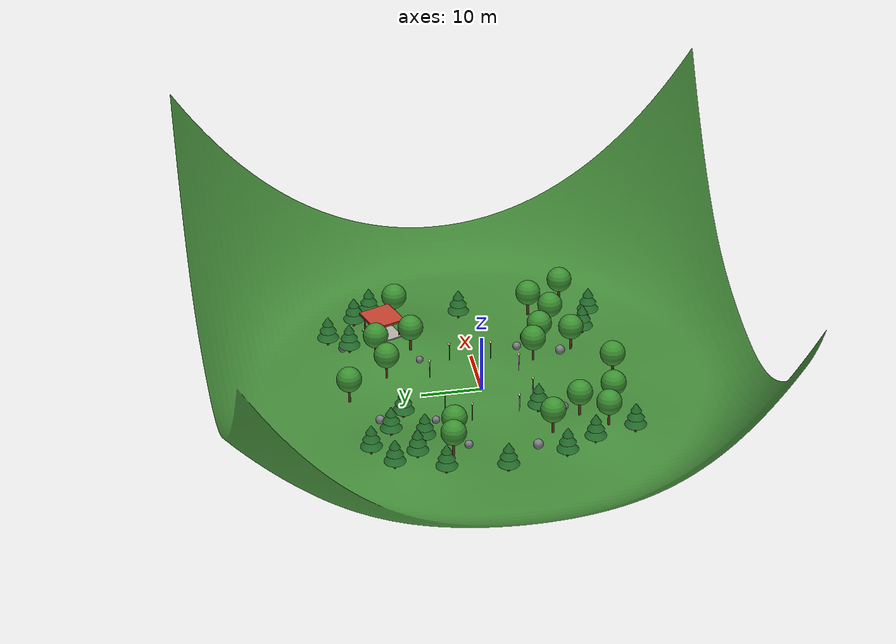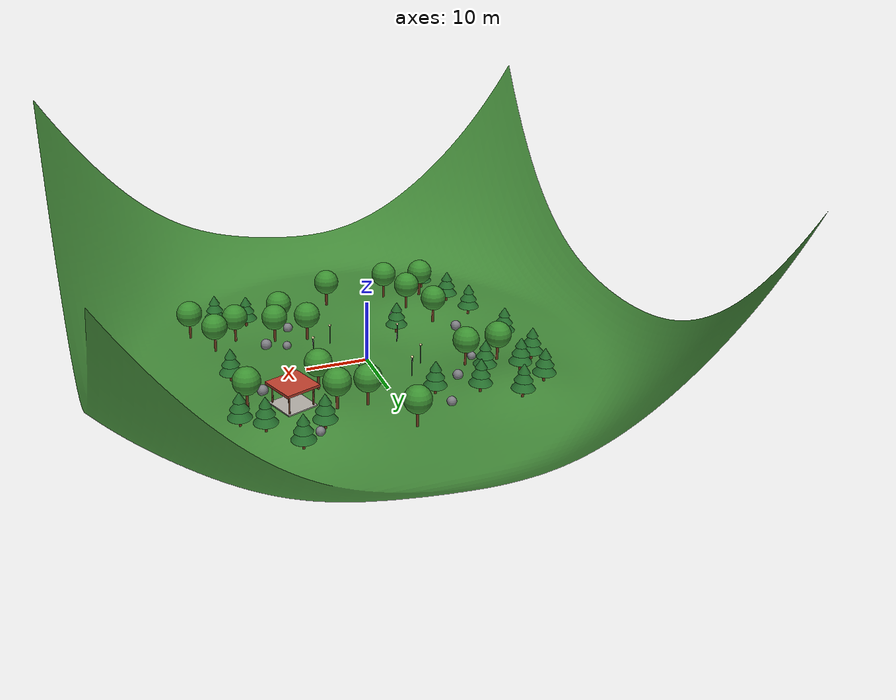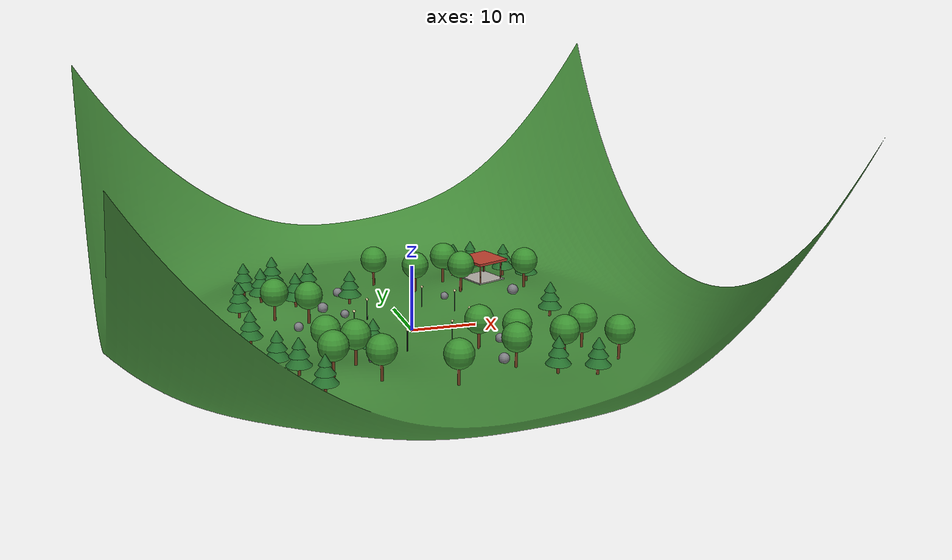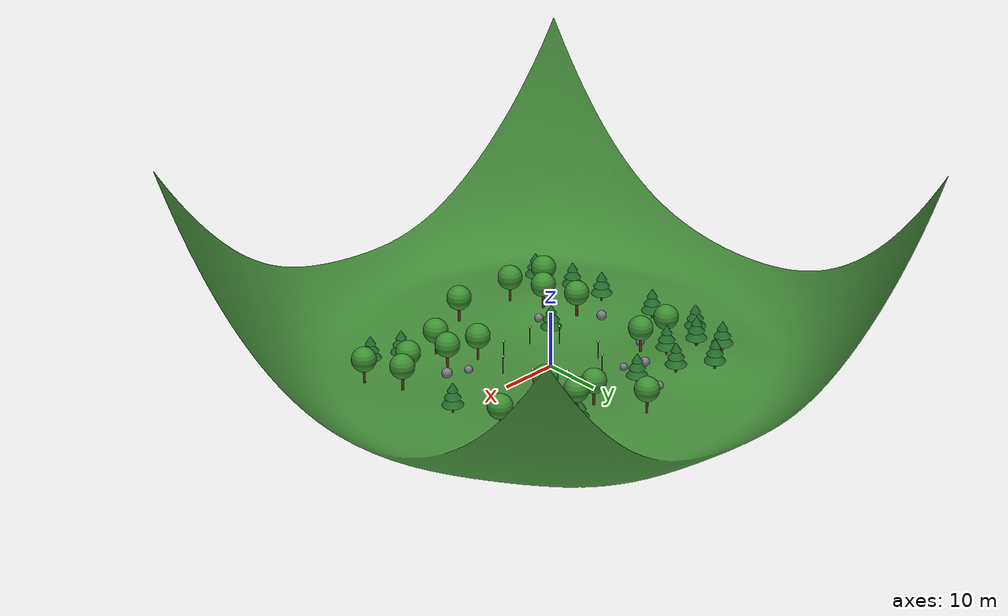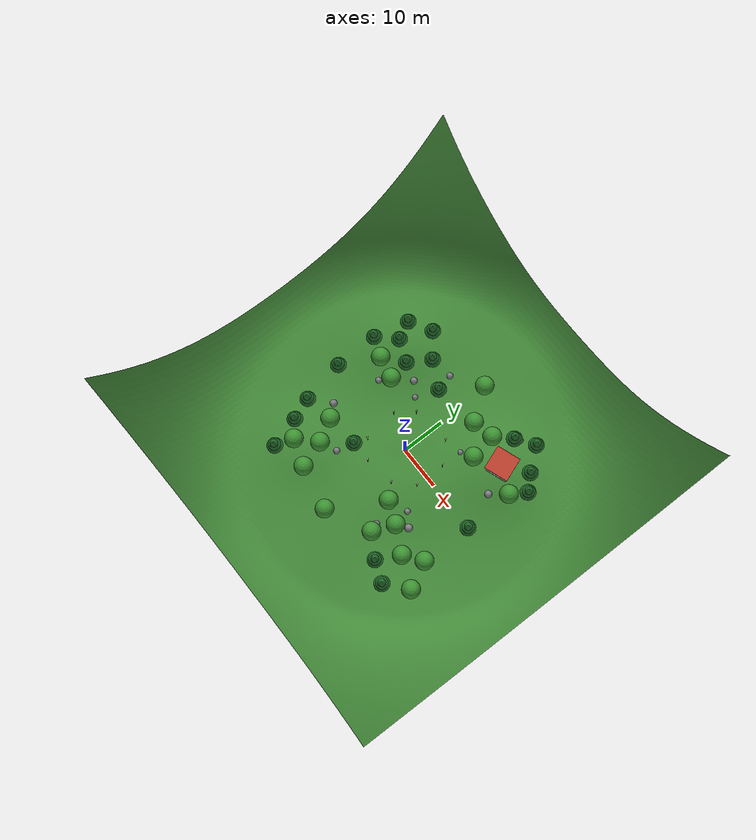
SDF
<?xml version="1.0" ?>
<sdf version="1.8">
  <model name="outdoor_park">
    <static>true</static>

    <!-- 1. 3D TERRAIN MESH (Rolling Hills, Slopes, and Meadow)          -->
    <link name="terrain_link">
      <collision name="terrain_collision">
        <geometry>
          <mesh>
            <uri>model://outdoor_park/meshes/terrain.dae</uri>
          </mesh>
        </geometry>
        <surface>
          <friction>
            <ode>
              <mu>1.2</mu>
              <mu2>1.2</mu2>
            </ode>
          </friction>
        </surface>
      </collision>
      <visual name="terrain_visual">
        <geometry>
          <mesh>
            <uri>model://outdoor_park/meshes/terrain.dae</uri>
          </mesh>
        </geometry>
      </visual>
    </link>

    <!-- Tree 1 (pine) at (-15.0, 12.0) -->
    <link name="tree_1">
      <pose>-15.00 12.00 1.24 0 0 0</pose>
      <!-- Trunk -->
      <collision name="trunk_col">
        <pose>0 0 1.60 0 0 0</pose>
        <geometry><cylinder><radius>0.2</radius><length>3.2</length></cylinder></geometry>
      </collision>
      <visual name="trunk_vis">
        <pose>0 0 1.60 0 0 0</pose>
        <geometry><cylinder><radius>0.2</radius><length>3.2</length></cylinder></geometry>
        <material>
          <ambient>0.35 0.20 0.10 1.0</ambient>
          <diffuse>0.45 0.25 0.12 1.0</diffuse>
        </material>
      </visual>
      <collision name="foliage_col_0">
        <pose>0 0 2.40 0 0 0</pose>
        <geometry><cone><radius>1.8</radius><length>2.0</length></cone></geometry>
      </collision>
      <visual name="foliage_vis_0">
        <pose>0 0 2.40 0 0 0</pose>
        <geometry><cone><radius>1.8</radius><length>2.0</length></cone></geometry>
        <material>
          <ambient>0.10 0.35 0.12 1.0</ambient>
          <diffuse>0.15 0.45 0.18 1.0</diffuse>
        </material>
      </visual>
      <collision name="foliage_col_1">
        <pose>0 0 3.60 0 0 0</pose>
        <geometry><cone><radius>1.4</radius><length>1.8</length></cone></geometry>
      </collision>
      <visual name="foliage_vis_1">
        <pose>0 0 3.60 0 0 0</pose>
        <geometry><cone><radius>1.4</radius><length>1.8</length></cone></geometry>
        <material>
          <ambient>0.10 0.35 0.12 1.0</ambient>
          <diffuse>0.15 0.45 0.18 1.0</diffuse>
        </material>
      </visual>
      <collision name="foliage_col_2">
        <pose>0 0 4.70 0 0 0</pose>
        <geometry><cone><radius>0.9</radius><length>1.5</length></cone></geometry>
      </collision>
      <visual name="foliage_vis_2">
        <pose>0 0 4.70 0 0 0</pose>
        <geometry><cone><radius>0.9</radius><length>1.5</length></cone></geometry>
        <material>
          <ambient>0.10 0.35 0.12 1.0</ambient>
          <diffuse>0.15 0.45 0.18 1.0</diffuse>
        </material>
      </visual>
    </link>

    <!-- Tree 2 (pine) at (-20.0, 14.0) -->
    <link name="tree_2">
      <pose>-20.00 14.00 1.80 0 0 0</pose>
      <!-- Trunk -->
      <collision name="trunk_col">
        <pose>0 0 1.60 0 0 0</pose>
        <geometry><cylinder><radius>0.2</radius><length>3.2</length></cylinder></geometry>
      </collision>
      <visual name="trunk_vis">
        <pose>0 0 1.60 0 0 0</pose>
        <geometry><cylinder><radius>0.2</radius><length>3.2</length></cylinder></geometry>
        <material>
          <ambient>0.35 0.20 0.10 1.0</ambient>
          <diffuse>0.45 0.25 0.12 1.0</diffuse>
        </material>
      </visual>
      <collision name="foliage_col_0">
        <pose>0 0 2.40 0 0 0</pose>
        <geometry><cone><radius>1.8</radius><length>2.0</length></cone></geometry>
      </collision>
      <visual name="foliage_vis_0">
        <pose>0 0 2.40 0 0 0</pose>
        <geometry><cone><radius>1.8</radius><length>2.0</length></cone></geometry>
        <material>
          <ambient>0.10 0.35 0.12 1.0</ambient>
          <diffuse>0.15 0.45 0.18 1.0</diffuse>
        </material>
      </visual>
      <collision name="foliage_col_1">
        <pose>0 0 3.60 0 0 0</pose>
        <geometry><cone><radius>1.4</radius><length>1.8</length></cone></geometry>
      </collision>
      <visual name="foliage_vis_1">
        <pose>0 0 3.60 0 0 0</pose>
        <geometry><cone><radius>1.4</radius><length>1.8</length></cone></geometry>
        <material>
          <ambient>0.10 0.35 0.12 1.0</ambient>
          <diffuse>0.15 0.45 0.18 1.0</diffuse>
        </material>
      </visual>
      <collision name="foliage_col_2">
        <pose>0 0 4.70 0 0 0</pose>
        <geometry><cone><radius>0.9</radius><length>1.5</length></cone></geometry>
      </collision>
      <visual name="foliage_vis_2">
        <pose>0 0 4.70 0 0 0</pose>
        <geometry><cone><radius>0.9</radius><length>1.5</length></cone></geometry>
        <material>
          <ambient>0.10 0.35 0.12 1.0</ambient>
          <diffuse>0.15 0.45 0.18 1.0</diffuse>
        </material>
      </visual>
    </link>

    <!-- Tree 3 (pine) at (-22.0, 18.0) -->
    <link name="tree_3">
      <pose>-22.00 18.00 1.60 0 0 0</pose>
      <!-- Trunk -->
      <collision name="trunk_col">
        <pose>0 0 1.60 0 0 0</pose>
        <geometry><cylinder><radius>0.2</radius><length>3.2</length></cylinder></geometry>
      </collision>
      <visual name="trunk_vis">
        <pose>0 0 1.60 0 0 0</pose>
        <geometry><cylinder><radius>0.2</radius><length>3.2</length></cylinder></geometry>
        <material>
          <ambient>0.35 0.20 0.10 1.0</ambient>
          <diffuse>0.45 0.25 0.12 1.0</diffuse>
        </material>
      </visual>
      <collision name="foliage_col_0">
        <pose>0 0 2.40 0 0 0</pose>
        <geometry><cone><radius>1.8</radius><length>2.0</length></cone></geometry>
      </collision>
      <visual name="foliage_vis_0">
        <pose>0 0 2.40 0 0 0</pose>
        <geometry><cone><radius>1.8</radius><length>2.0</length></cone></geometry>
        <material>
          <ambient>0.10 0.35 0.12 1.0</ambient>
          <diffuse>0.15 0.45 0.18 1.0</diffuse>
        </material>
      </visual>
      <collision name="foliage_col_1">
        <pose>0 0 3.60 0 0 0</pose>
        <geometry><cone><radius>1.4</radius><length>1.8</length></cone></geometry>
      </collision>
      <visual name="foliage_vis_1">
        <pose>0 0 3.60 0 0 0</pose>
        <geometry><cone><radius>1.4</radius><length>1.8</length></cone></geometry>
        <material>
          <ambient>0.10 0.35 0.12 1.0</ambient>
          <diffuse>0.15 0.45 0.18 1.0</diffuse>
        </material>
      </visual>
      <collision name="foliage_col_2">
        <pose>0 0 4.70 0 0 0</pose>
        <geometry><cone><radius>0.9</radius><length>1.5</length></cone></geometry>
      </collision>
      <visual name="foliage_vis_2">
        <pose>0 0 4.70 0 0 0</pose>
        <geometry><cone><radius>0.9</radius><length>1.5</length></cone></geometry>
        <material>
          <ambient>0.10 0.35 0.12 1.0</ambient>
          <diffuse>0.15 0.45 0.18 1.0</diffuse>
        </material>
      </visual>
    </link>

    <!-- Tree 4 (pine) at (-17.0, 21.0) -->
    <link name="tree_4">
      <pose>-17.00 21.00 1.38 0 0 0</pose>
      <!-- Trunk -->
      <collision name="trunk_col">
        <pose>0 0 1.60 0 0 0</pose>
        <geometry><cylinder><radius>0.2</radius><length>3.2</length></cylinder></geometry>
      </collision>
      <visual name="trunk_vis">
        <pose>0 0 1.60 0 0 0</pose>
        <geometry><cylinder><radius>0.2</radius><length>3.2</length></cylinder></geometry>
        <material>
          <ambient>0.35 0.20 0.10 1.0</ambient>
          <diffuse>0.45 0.25 0.12 1.0</diffuse>
        </material>
      </visual>
      <collision name="foliage_col_0">
        <pose>0 0 2.40 0 0 0</pose>
        <geometry><cone><radius>1.8</radius><length>2.0</length></cone></geometry>
      </collision>
      <visual name="foliage_vis_0">
        <pose>0 0 2.40 0 0 0</pose>
        <geometry><cone><radius>1.8</radius><length>2.0</length></cone></geometry>
        <material>
          <ambient>0.10 0.35 0.12 1.0</ambient>
          <diffuse>0.15 0.45 0.18 1.0</diffuse>
        </material>
      </visual>
      <collision name="foliage_col_1">
        <pose>0 0 3.60 0 0 0</pose>
        <geometry><cone><radius>1.4</radius><length>1.8</length></cone></geometry>
      </collision>
      <visual name="foliage_vis_1">
        <pose>0 0 3.60 0 0 0</pose>
        <geometry><cone><radius>1.4</radius><length>1.8</length></cone></geometry>
        <material>
          <ambient>0.10 0.35 0.12 1.0</ambient>
          <diffuse>0.15 0.45 0.18 1.0</diffuse>
        </material>
      </visual>
      <collision name="foliage_col_2">
        <pose>0 0 4.70 0 0 0</pose>
        <geometry><cone><radius>0.9</radius><length>1.5</length></cone></geometry>
      </collision>
      <visual name="foliage_vis_2">
        <pose>0 0 4.70 0 0 0</pose>
        <geometry><cone><radius>0.9</radius><length>1.5</length></cone></geometry>
        <material>
          <ambient>0.10 0.35 0.12 1.0</ambient>
          <diffuse>0.15 0.45 0.18 1.0</diffuse>
        </material>
      </visual>
    </link>

    <!-- Tree 5 (pine) at (-12.0, 17.0) -->
    <link name="tree_5">
      <pose>-12.00 17.00 1.07 0 0 0</pose>
      <!-- Trunk -->
      <collision name="trunk_col">
        <pose>0 0 1.60 0 0 0</pose>
        <geometry><cylinder><radius>0.2</radius><length>3.2</length></cylinder></geometry>
      </collision>
      <visual name="trunk_vis">
        <pose>0 0 1.60 0 0 0</pose>
        <geometry><cylinder><radius>0.2</radius><length>3.2</length></cylinder></geometry>
        <material>
          <ambient>0.35 0.20 0.10 1.0</ambient>
          <diffuse>0.45 0.25 0.12 1.0</diffuse>
        </material>
      </visual>
      <collision name="foliage_col_0">
        <pose>0 0 2.40 0 0 0</pose>
        <geometry><cone><radius>1.8</radius><length>2.0</length></cone></geometry>
      </collision>
      <visual name="foliage_vis_0">
        <pose>0 0 2.40 0 0 0</pose>
        <geometry><cone><radius>1.8</radius><length>2.0</length></cone></geometry>
        <material>
          <ambient>0.10 0.35 0.12 1.0</ambient>
          <diffuse>0.15 0.45 0.18 1.0</diffuse>
        </material>
      </visual>
      <collision name="foliage_col_1">
        <pose>0 0 3.60 0 0 0</pose>
        <geometry><cone><radius>1.4</radius><length>1.8</length></cone></geometry>
      </collision>
      <visual name="foliage_vis_1">
        <pose>0 0 3.60 0 0 0</pose>
        <geometry><cone><radius>1.4</radius><length>1.8</length></cone></geometry>
        <material>
          <ambient>0.10 0.35 0.12 1.0</ambient>
          <diffuse>0.15 0.45 0.18 1.0</diffuse>
        </material>
      </visual>
      <collision name="foliage_col_2">
        <pose>0 0 4.70 0 0 0</pose>
        <geometry><cone><radius>0.9</radius><length>1.5</length></cone></geometry>
      </collision>
      <visual name="foliage_vis_2">
        <pose>0 0 4.70 0 0 0</pose>
        <geometry><cone><radius>0.9</radius><length>1.5</length></cone></geometry>
        <material>
          <ambient>0.10 0.35 0.12 1.0</ambient>
          <diffuse>0.15 0.45 0.18 1.0</diffuse>
        </material>
      </visual>
    </link>

    <!-- Tree 6 (pine) at (-24.0, 10.0) -->
    <link name="tree_6">
      <pose>-24.00 10.00 1.05 0 0 0</pose>
      <!-- Trunk -->
      <collision name="trunk_col">
        <pose>0 0 1.60 0 0 0</pose>
        <geometry><cylinder><radius>0.2</radius><length>3.2</length></cylinder></geometry>
      </collision>
      <visual name="trunk_vis">
        <pose>0 0 1.60 0 0 0</pose>
        <geometry><cylinder><radius>0.2</radius><length>3.2</length></cylinder></geometry>
        <material>
          <ambient>0.35 0.20 0.10 1.0</ambient>
          <diffuse>0.45 0.25 0.12 1.0</diffuse>
        </material>
      </visual>
      <collision name="foliage_col_0">
        <pose>0 0 2.40 0 0 0</pose>
        <geometry><cone><radius>1.8</radius><length>2.0</length></cone></geometry>
      </collision>
      <visual name="foliage_vis_0">
        <pose>0 0 2.40 0 0 0</pose>
        <geometry><cone><radius>1.8</radius><length>2.0</length></cone></geometry>
        <material>
          <ambient>0.10 0.35 0.12 1.0</ambient>
          <diffuse>0.15 0.45 0.18 1.0</diffuse>
        </material>
      </visual>
      <collision name="foliage_col_1">
        <pose>0 0 3.60 0 0 0</pose>
        <geometry><cone><radius>1.4</radius><length>1.8</length></cone></geometry>
      </collision>
      <visual name="foliage_vis_1">
        <pose>0 0 3.60 0 0 0</pose>
        <geometry><cone><radius>1.4</radius><length>1.8</length></cone></geometry>
        <material>
          <ambient>0.10 0.35 0.12 1.0</ambient>
          <diffuse>0.15 0.45 0.18 1.0</diffuse>
        </material>
      </visual>
      <collision name="foliage_col_2">
        <pose>0 0 4.70 0 0 0</pose>
        <geometry><cone><radius>0.9</radius><length>1.5</length></cone></geometry>
      </collision>
      <visual name="foliage_vis_2">
        <pose>0 0 4.70 0 0 0</pose>
        <geometry><cone><radius>0.9</radius><length>1.5</length></cone></geometry>
        <material>
          <ambient>0.10 0.35 0.12 1.0</ambient>
          <diffuse>0.15 0.45 0.18 1.0</diffuse>
        </material>
      </visual>
    </link>

    <!-- Tree 7 (broadleaf) at (-19.0, 8.0) -->
    <link name="tree_7">
      <pose>-19.00 8.00 0.81 0 0 0</pose>
      <!-- Trunk -->
      <collision name="trunk_col">
        <pose>0 0 1.60 0 0 0</pose>
        <geometry><cylinder><radius>0.2</radius><length>3.2</length></cylinder></geometry>
      </collision>
      <visual name="trunk_vis">
        <pose>0 0 1.60 0 0 0</pose>
        <geometry><cylinder><radius>0.2</radius><length>3.2</length></cylinder></geometry>
        <material>
          <ambient>0.35 0.20 0.10 1.0</ambient>
          <diffuse>0.45 0.25 0.12 1.0</diffuse>
        </material>
      </visual>
      <collision name="foliage_col">
        <pose>0 0 4.40 0 0 0</pose>
        <geometry><sphere><radius>2.1</radius></sphere></geometry>
      </collision>
      <visual name="foliage_vis">
        <pose>0 0 4.40 0 0 0</pose>
        <geometry><sphere><radius>2.1</radius></sphere></geometry>
        <material>
          <ambient>0.18 0.48 0.15 1.0</ambient>
          <diffuse>0.24 0.58 0.20 1.0</diffuse>
        </material>
      </visual>
    </link>

    <!-- Tree 8 (broadleaf) at (-14.0, 7.0) -->
    <link name="tree_8">
      <pose>-14.00 7.00 0.21 0 0 0</pose>
      <!-- Trunk -->
      <collision name="trunk_col">
        <pose>0 0 1.60 0 0 0</pose>
        <geometry><cylinder><radius>0.2</radius><length>3.2</length></cylinder></geometry>
      </collision>
      <visual name="trunk_vis">
        <pose>0 0 1.60 0 0 0</pose>
        <geometry><cylinder><radius>0.2</radius><length>3.2</length></cylinder></geometry>
        <material>
          <ambient>0.35 0.20 0.10 1.0</ambient>
          <diffuse>0.45 0.25 0.12 1.0</diffuse>
        </material>
      </visual>
      <collision name="foliage_col">
        <pose>0 0 4.40 0 0 0</pose>
        <geometry><sphere><radius>2.1</radius></sphere></geometry>
      </collision>
      <visual name="foliage_vis">
        <pose>0 0 4.40 0 0 0</pose>
        <geometry><sphere><radius>2.1</radius></sphere></geometry>
        <material>
          <ambient>0.18 0.48 0.15 1.0</ambient>
          <diffuse>0.24 0.58 0.20 1.0</diffuse>
        </material>
      </visual>
    </link>

    <!-- Tree 9 (broadleaf) at (-12.0, -14.0) -->
    <link name="tree_9">
      <pose>-12.00 -14.00 1.27 0 0 0</pose>
      <!-- Trunk -->
      <collision name="trunk_col">
        <pose>0 0 1.60 0 0 0</pose>
        <geometry><cylinder><radius>0.2</radius><length>3.2</length></cylinder></geometry>
      </collision>
      <visual name="trunk_vis">
        <pose>0 0 1.60 0 0 0</pose>
        <geometry><cylinder><radius>0.2</radius><length>3.2</length></cylinder></geometry>
        <material>
          <ambient>0.35 0.20 0.10 1.0</ambient>
          <diffuse>0.45 0.25 0.12 1.0</diffuse>
        </material>
      </visual>
      <collision name="foliage_col">
        <pose>0 0 4.40 0 0 0</pose>
        <geometry><sphere><radius>2.1</radius></sphere></geometry>
      </collision>
      <visual name="foliage_vis">
        <pose>0 0 4.40 0 0 0</pose>
        <geometry><sphere><radius>2.1</radius></sphere></geometry>
        <material>
          <ambient>0.18 0.48 0.15 1.0</ambient>
          <diffuse>0.24 0.58 0.20 1.0</diffuse>
        </material>
      </visual>
    </link>

    <!-- Tree 10 (broadleaf) at (-16.0, -18.0) -->
    <link name="tree_10">
      <pose>-16.00 -18.00 1.54 0 0 0</pose>
      <!-- Trunk -->
      <collision name="trunk_col">
        <pose>0 0 1.60 0 0 0</pose>
        <geometry><cylinder><radius>0.2</radius><length>3.2</length></cylinder></geometry>
      </collision>
      <visual name="trunk_vis">
        <pose>0 0 1.60 0 0 0</pose>
        <geometry><cylinder><radius>0.2</radius><length>3.2</length></cylinder></geometry>
        <material>
          <ambient>0.35 0.20 0.10 1.0</ambient>
          <diffuse>0.45 0.25 0.12 1.0</diffuse>
        </material>
      </visual>
      <collision name="foliage_col">
        <pose>0 0 4.40 0 0 0</pose>
        <geometry><sphere><radius>2.1</radius></sphere></geometry>
      </collision>
      <visual name="foliage_vis">
        <pose>0 0 4.40 0 0 0</pose>
        <geometry><sphere><radius>2.1</radius></sphere></geometry>
        <material>
          <ambient>0.18 0.48 0.15 1.0</ambient>
          <diffuse>0.24 0.58 0.20 1.0</diffuse>
        </material>
      </visual>
    </link>

    <!-- Tree 11 (pine) at (-20.0, -15.0) -->
    <link name="tree_11">
      <pose>-20.00 -15.00 1.08 0 0 0</pose>
      <!-- Trunk -->
      <collision name="trunk_col">
        <pose>0 0 1.60 0 0 0</pose>
        <geometry><cylinder><radius>0.2</radius><length>3.2</length></cylinder></geometry>
      </collision>
      <visual name="trunk_vis">
        <pose>0 0 1.60 0 0 0</pose>
        <geometry><cylinder><radius>0.2</radius><length>3.2</length></cylinder></geometry>
        <material>
          <ambient>0.35 0.20 0.10 1.0</ambient>
          <diffuse>0.45 0.25 0.12 1.0</diffuse>
        </material>
      </visual>
      <collision name="foliage_col_0">
        <pose>0 0 2.40 0 0 0</pose>
        <geometry><cone><radius>1.8</radius><length>2.0</length></cone></geometry>
      </collision>
      <visual name="foliage_vis_0">
        <pose>0 0 2.40 0 0 0</pose>
        <geometry><cone><radius>1.8</radius><length>2.0</length></cone></geometry>
        <material>
          <ambient>0.10 0.35 0.12 1.0</ambient>
          <diffuse>0.15 0.45 0.18 1.0</diffuse>
        </material>
      </visual>
      <collision name="foliage_col_1">
        <pose>0 0 3.60 0 0 0</pose>
        <geometry><cone><radius>1.4</radius><length>1.8</length></cone></geometry>
      </collision>
      <visual name="foliage_vis_1">
        <pose>0 0 3.60 0 0 0</pose>
        <geometry><cone><radius>1.4</radius><length>1.8</length></cone></geometry>
        <material>
          <ambient>0.10 0.35 0.12 1.0</ambient>
          <diffuse>0.15 0.45 0.18 1.0</diffuse>
        </material>
      </visual>
      <collision name="foliage_col_2">
        <pose>0 0 4.70 0 0 0</pose>
        <geometry><cone><radius>0.9</radius><length>1.5</length></cone></geometry>
      </collision>
      <visual name="foliage_vis_2">
        <pose>0 0 4.70 0 0 0</pose>
        <geometry><cone><radius>0.9</radius><length>1.5</length></cone></geometry>
        <material>
          <ambient>0.10 0.35 0.12 1.0</ambient>
          <diffuse>0.15 0.45 0.18 1.0</diffuse>
        </material>
      </visual>
    </link>

    <!-- Tree 12 (pine) at (-18.0, -22.0) -->
    <link name="tree_12">
      <pose>-18.00 -22.00 1.06 0 0 0</pose>
      <!-- Trunk -->
      <collision name="trunk_col">
        <pose>0 0 1.60 0 0 0</pose>
        <geometry><cylinder><radius>0.2</radius><length>3.2</length></cylinder></geometry>
      </collision>
      <visual name="trunk_vis">
        <pose>0 0 1.60 0 0 0</pose>
        <geometry><cylinder><radius>0.2</radius><length>3.2</length></cylinder></geometry>
        <material>
          <ambient>0.35 0.20 0.10 1.0</ambient>
          <diffuse>0.45 0.25 0.12 1.0</diffuse>
        </material>
      </visual>
      <collision name="foliage_col_0">
        <pose>0 0 2.40 0 0 0</pose>
        <geometry><cone><radius>1.8</radius><length>2.0</length></cone></geometry>
      </collision>
      <visual name="foliage_vis_0">
        <pose>0 0 2.40 0 0 0</pose>
        <geometry><cone><radius>1.8</radius><length>2.0</length></cone></geometry>
        <material>
          <ambient>0.10 0.35 0.12 1.0</ambient>
          <diffuse>0.15 0.45 0.18 1.0</diffuse>
        </material>
      </visual>
      <collision name="foliage_col_1">
        <pose>0 0 3.60 0 0 0</pose>
        <geometry><cone><radius>1.4</radius><length>1.8</length></cone></geometry>
      </collision>
      <visual name="foliage_vis_1">
        <pose>0 0 3.60 0 0 0</pose>
        <geometry><cone><radius>1.4</radius><length>1.8</length></cone></geometry>
        <material>
          <ambient>0.10 0.35 0.12 1.0</ambient>
          <diffuse>0.15 0.45 0.18 1.0</diffuse>
        </material>
      </visual>
      <collision name="foliage_col_2">
        <pose>0 0 4.70 0 0 0</pose>
        <geometry><cone><radius>0.9</radius><length>1.5</length></cone></geometry>
      </collision>
      <visual name="foliage_vis_2">
        <pose>0 0 4.70 0 0 0</pose>
        <geometry><cone><radius>0.9</radius><length>1.5</length></cone></geometry>
        <material>
          <ambient>0.10 0.35 0.12 1.0</ambient>
          <diffuse>0.15 0.45 0.18 1.0</diffuse>
        </material>
      </visual>
    </link>

    <!-- Tree 13 (broadleaf) at (-10.0, -20.0) -->
    <link name="tree_13">
      <pose>-10.00 -20.00 1.11 0 0 0</pose>
      <!-- Trunk -->
      <collision name="trunk_col">
        <pose>0 0 1.60 0 0 0</pose>
        <geometry><cylinder><radius>0.2</radius><length>3.2</length></cylinder></geometry>
      </collision>
      <visual name="trunk_vis">
        <pose>0 0 1.60 0 0 0</pose>
        <geometry><cylinder><radius>0.2</radius><length>3.2</length></cylinder></geometry>
        <material>
          <ambient>0.35 0.20 0.10 1.0</ambient>
          <diffuse>0.45 0.25 0.12 1.0</diffuse>
        </material>
      </visual>
      <collision name="foliage_col">
        <pose>0 0 4.40 0 0 0</pose>
        <geometry><sphere><radius>2.1</radius></sphere></geometry>
      </collision>
      <visual name="foliage_vis">
        <pose>0 0 4.40 0 0 0</pose>
        <geometry><sphere><radius>2.1</radius></sphere></geometry>
        <material>
          <ambient>0.18 0.48 0.15 1.0</ambient>
          <diffuse>0.24 0.58 0.20 1.0</diffuse>
        </material>
      </visual>
    </link>

    <!-- Tree 14 (pine) at (-22.0, -10.0) -->
    <link name="tree_14">
      <pose>-22.00 -10.00 0.45 0 0 0</pose>
      <!-- Trunk -->
      <collision name="trunk_col">
        <pose>0 0 1.60 0 0 0</pose>
        <geometry><cylinder><radius>0.2</radius><length>3.2</length></cylinder></geometry>
      </collision>
      <visual name="trunk_vis">
        <pose>0 0 1.60 0 0 0</pose>
        <geometry><cylinder><radius>0.2</radius><length>3.2</length></cylinder></geometry>
        <material>
          <ambient>0.35 0.20 0.10 1.0</ambient>
          <diffuse>0.45 0.25 0.12 1.0</diffuse>
        </material>
      </visual>
      <collision name="foliage_col_0">
        <pose>0 0 2.40 0 0 0</pose>
        <geometry><cone><radius>1.8</radius><length>2.0</length></cone></geometry>
      </collision>
      <visual name="foliage_vis_0">
        <pose>0 0 2.40 0 0 0</pose>
        <geometry><cone><radius>1.8</radius><length>2.0</length></cone></geometry>
        <material>
          <ambient>0.10 0.35 0.12 1.0</ambient>
          <diffuse>0.15 0.45 0.18 1.0</diffuse>
        </material>
      </visual>
      <collision name="foliage_col_1">
        <pose>0 0 3.60 0 0 0</pose>
        <geometry><cone><radius>1.4</radius><length>1.8</length></cone></geometry>
      </collision>
      <visual name="foliage_vis_1">
        <pose>0 0 3.60 0 0 0</pose>
        <geometry><cone><radius>1.4</radius><length>1.8</length></cone></geometry>
        <material>
          <ambient>0.10 0.35 0.12 1.0</ambient>
          <diffuse>0.15 0.45 0.18 1.0</diffuse>
        </material>
      </visual>
      <collision name="foliage_col_2">
        <pose>0 0 4.70 0 0 0</pose>
        <geometry><cone><radius>0.9</radius><length>1.5</length></cone></geometry>
      </collision>
      <visual name="foliage_vis_2">
        <pose>0 0 4.70 0 0 0</pose>
        <geometry><cone><radius>0.9</radius><length>1.5</length></cone></geometry>
        <material>
          <ambient>0.10 0.35 0.12 1.0</ambient>
          <diffuse>0.15 0.45 0.18 1.0</diffuse>
        </material>
      </visual>
    </link>

    <!-- Tree 15 (broadleaf) at (-15.0, -9.0) -->
    <link name="tree_15">
      <pose>-15.00 -9.00 0.45 0 0 0</pose>
      <!-- Trunk -->
      <collision name="trunk_col">
        <pose>0 0 1.60 0 0 0</pose>
        <geometry><cylinder><radius>0.2</radius><length>3.2</length></cylinder></geometry>
      </collision>
      <visual name="trunk_vis">
        <pose>0 0 1.60 0 0 0</pose>
        <geometry><cylinder><radius>0.2</radius><length>3.2</length></cylinder></geometry>
        <material>
          <ambient>0.35 0.20 0.10 1.0</ambient>
          <diffuse>0.45 0.25 0.12 1.0</diffuse>
        </material>
      </visual>
      <collision name="foliage_col">
        <pose>0 0 4.40 0 0 0</pose>
        <geometry><sphere><radius>2.1</radius></sphere></geometry>
      </collision>
      <visual name="foliage_vis">
        <pose>0 0 4.40 0 0 0</pose>
        <geometry><sphere><radius>2.1</radius></sphere></geometry>
        <material>
          <ambient>0.18 0.48 0.15 1.0</ambient>
          <diffuse>0.24 0.58 0.20 1.0</diffuse>
        </material>
      </visual>
    </link>

    <!-- Tree 16 (broadleaf) at (12.0, -12.0) -->
    <link name="tree_16">
      <pose>12.00 -12.00 -0.35 0 0 0</pose>
      <!-- Trunk -->
      <collision name="trunk_col">
        <pose>0 0 1.60 0 0 0</pose>
        <geometry><cylinder><radius>0.2</radius><length>3.2</length></cylinder></geometry>
      </collision>
      <visual name="trunk_vis">
        <pose>0 0 1.60 0 0 0</pose>
        <geometry><cylinder><radius>0.2</radius><length>3.2</length></cylinder></geometry>
        <material>
          <ambient>0.35 0.20 0.10 1.0</ambient>
          <diffuse>0.45 0.25 0.12 1.0</diffuse>
        </material>
      </visual>
      <collision name="foliage_col">
        <pose>0 0 4.40 0 0 0</pose>
        <geometry><sphere><radius>2.1</radius></sphere></geometry>
      </collision>
      <visual name="foliage_vis">
        <pose>0 0 4.40 0 0 0</pose>
        <geometry><sphere><radius>2.1</radius></sphere></geometry>
        <material>
          <ambient>0.18 0.48 0.15 1.0</ambient>
          <diffuse>0.24 0.58 0.20 1.0</diffuse>
        </material>
      </visual>
    </link>

    <!-- Tree 17 (broadleaf) at (18.0, -15.0) -->
    <link name="tree_17">
      <pose>18.00 -15.00 -0.77 0 0 0</pose>
      <!-- Trunk -->
      <collision name="trunk_col">
        <pose>0 0 1.60 0 0 0</pose>
        <geometry><cylinder><radius>0.2</radius><length>3.2</length></cylinder></geometry>
      </collision>
      <visual name="trunk_vis">
        <pose>0 0 1.60 0 0 0</pose>
        <geometry><cylinder><radius>0.2</radius><length>3.2</length></cylinder></geometry>
        <material>
          <ambient>0.35 0.20 0.10 1.0</ambient>
          <diffuse>0.45 0.25 0.12 1.0</diffuse>
        </material>
      </visual>
      <collision name="foliage_col">
        <pose>0 0 4.40 0 0 0</pose>
        <geometry><sphere><radius>2.1</radius></sphere></geometry>
      </collision>
      <visual name="foliage_vis">
        <pose>0 0 4.40 0 0 0</pose>
        <geometry><sphere><radius>2.1</radius></sphere></geometry>
        <material>
          <ambient>0.18 0.48 0.15 1.0</ambient>
          <diffuse>0.24 0.58 0.20 1.0</diffuse>
        </material>
      </visual>
    </link>

    <!-- Tree 18 (broadleaf) at (22.0, -12.0) -->
    <link name="tree_18">
      <pose>22.00 -12.00 -0.54 0 0 0</pose>
      <!-- Trunk -->
      <collision name="trunk_col">
        <pose>0 0 1.60 0 0 0</pose>
        <geometry><cylinder><radius>0.2</radius><length>3.2</length></cylinder></geometry>
      </collision>
      <visual name="trunk_vis">
        <pose>0 0 1.60 0 0 0</pose>
        <geometry><cylinder><radius>0.2</radius><length>3.2</length></cylinder></geometry>
        <material>
          <ambient>0.35 0.20 0.10 1.0</ambient>
          <diffuse>0.45 0.25 0.12 1.0</diffuse>
        </material>
      </visual>
      <collision name="foliage_col">
        <pose>0 0 4.40 0 0 0</pose>
        <geometry><sphere><radius>2.1</radius></sphere></geometry>
      </collision>
      <visual name="foliage_vis">
        <pose>0 0 4.40 0 0 0</pose>
        <geometry><sphere><radius>2.1</radius></sphere></geometry>
        <material>
          <ambient>0.18 0.48 0.15 1.0</ambient>
          <diffuse>0.24 0.58 0.20 1.0</diffuse>
        </material>
      </visual>
    </link>

    <!-- Tree 19 (pine) at (15.0, -20.0) -->
    <link name="tree_19">
      <pose>15.00 -20.00 -0.69 0 0 0</pose>
      <!-- Trunk -->
      <collision name="trunk_col">
        <pose>0 0 1.60 0 0 0</pose>
        <geometry><cylinder><radius>0.2</radius><length>3.2</length></cylinder></geometry>
      </collision>
      <visual name="trunk_vis">
        <pose>0 0 1.60 0 0 0</pose>
        <geometry><cylinder><radius>0.2</radius><length>3.2</length></cylinder></geometry>
        <material>
          <ambient>0.35 0.20 0.10 1.0</ambient>
          <diffuse>0.45 0.25 0.12 1.0</diffuse>
        </material>
      </visual>
      <collision name="foliage_col_0">
        <pose>0 0 2.40 0 0 0</pose>
        <geometry><cone><radius>1.8</radius><length>2.0</length></cone></geometry>
      </collision>
      <visual name="foliage_vis_0">
        <pose>0 0 2.40 0 0 0</pose>
        <geometry><cone><radius>1.8</radius><length>2.0</length></cone></geometry>
        <material>
          <ambient>0.10 0.35 0.12 1.0</ambient>
          <diffuse>0.15 0.45 0.18 1.0</diffuse>
        </material>
      </visual>
      <collision name="foliage_col_1">
        <pose>0 0 3.60 0 0 0</pose>
        <geometry><cone><radius>1.4</radius><length>1.8</length></cone></geometry>
      </collision>
      <visual name="foliage_vis_1">
        <pose>0 0 3.60 0 0 0</pose>
        <geometry><cone><radius>1.4</radius><length>1.8</length></cone></geometry>
        <material>
          <ambient>0.10 0.35 0.12 1.0</ambient>
          <diffuse>0.15 0.45 0.18 1.0</diffuse>
        </material>
      </visual>
      <collision name="foliage_col_2">
        <pose>0 0 4.70 0 0 0</pose>
        <geometry><cone><radius>0.9</radius><length>1.5</length></cone></geometry>
      </collision>
      <visual name="foliage_vis_2">
        <pose>0 0 4.70 0 0 0</pose>
        <geometry><cone><radius>0.9</radius><length>1.5</length></cone></geometry>
        <material>
          <ambient>0.10 0.35 0.12 1.0</ambient>
          <diffuse>0.15 0.45 0.18 1.0</diffuse>
        </material>
      </visual>
    </link>

    <!-- Tree 20 (pine) at (20.0, -22.0) -->
    <link name="tree_20">
      <pose>20.00 -22.00 -0.65 0 0 0</pose>
      <!-- Trunk -->
      <collision name="trunk_col">
        <pose>0 0 1.60 0 0 0</pose>
        <geometry><cylinder><radius>0.2</radius><length>3.2</length></cylinder></geometry>
      </collision>
      <visual name="trunk_vis">
        <pose>0 0 1.60 0 0 0</pose>
        <geometry><cylinder><radius>0.2</radius><length>3.2</length></cylinder></geometry>
        <material>
          <ambient>0.35 0.20 0.10 1.0</ambient>
          <diffuse>0.45 0.25 0.12 1.0</diffuse>
        </material>
      </visual>
      <collision name="foliage_col_0">
        <pose>0 0 2.40 0 0 0</pose>
        <geometry><cone><radius>1.8</radius><length>2.0</length></cone></geometry>
      </collision>
      <visual name="foliage_vis_0">
        <pose>0 0 2.40 0 0 0</pose>
        <geometry><cone><radius>1.8</radius><length>2.0</length></cone></geometry>
        <material>
          <ambient>0.10 0.35 0.12 1.0</ambient>
          <diffuse>0.15 0.45 0.18 1.0</diffuse>
        </material>
      </visual>
      <collision name="foliage_col_1">
        <pose>0 0 3.60 0 0 0</pose>
        <geometry><cone><radius>1.4</radius><length>1.8</length></cone></geometry>
      </collision>
      <visual name="foliage_vis_1">
        <pose>0 0 3.60 0 0 0</pose>
        <geometry><cone><radius>1.4</radius><length>1.8</length></cone></geometry>
        <material>
          <ambient>0.10 0.35 0.12 1.0</ambient>
          <diffuse>0.15 0.45 0.18 1.0</diffuse>
        </material>
      </visual>
      <collision name="foliage_col_2">
        <pose>0 0 4.70 0 0 0</pose>
        <geometry><cone><radius>0.9</radius><length>1.5</length></cone></geometry>
      </collision>
      <visual name="foliage_vis_2">
        <pose>0 0 4.70 0 0 0</pose>
        <geometry><cone><radius>0.9</radius><length>1.5</length></cone></geometry>
        <material>
          <ambient>0.10 0.35 0.12 1.0</ambient>
          <diffuse>0.15 0.45 0.18 1.0</diffuse>
        </material>
      </visual>
    </link>

    <!-- Tree 21 (broadleaf) at (10.0, -17.0) -->
    <link name="tree_21">
      <pose>10.00 -17.00 -0.38 0 0 0</pose>
      <!-- Trunk -->
      <collision name="trunk_col">
        <pose>0 0 1.60 0 0 0</pose>
        <geometry><cylinder><radius>0.2</radius><length>3.2</length></cylinder></geometry>
      </collision>
      <visual name="trunk_vis">
        <pose>0 0 1.60 0 0 0</pose>
        <geometry><cylinder><radius>0.2</radius><length>3.2</length></cylinder></geometry>
        <material>
          <ambient>0.35 0.20 0.10 1.0</ambient>
          <diffuse>0.45 0.25 0.12 1.0</diffuse>
        </material>
      </visual>
      <collision name="foliage_col">
        <pose>0 0 4.40 0 0 0</pose>
        <geometry><sphere><radius>2.1</radius></sphere></geometry>
      </collision>
      <visual name="foliage_vis">
        <pose>0 0 4.40 0 0 0</pose>
        <geometry><sphere><radius>2.1</radius></sphere></geometry>
        <material>
          <ambient>0.18 0.48 0.15 1.0</ambient>
          <diffuse>0.24 0.58 0.20 1.0</diffuse>
        </material>
      </visual>
    </link>

    <!-- Tree 22 (broadleaf) at (25.0, -18.0) -->
    <link name="tree_22">
      <pose>25.00 -18.00 -0.44 0 0 0</pose>
      <!-- Trunk -->
      <collision name="trunk_col">
        <pose>0 0 1.60 0 0 0</pose>
        <geometry><cylinder><radius>0.2</radius><length>3.2</length></cylinder></geometry>
      </collision>
      <visual name="trunk_vis">
        <pose>0 0 1.60 0 0 0</pose>
        <geometry><cylinder><radius>0.2</radius><length>3.2</length></cylinder></geometry>
        <material>
          <ambient>0.35 0.20 0.10 1.0</ambient>
          <diffuse>0.45 0.25 0.12 1.0</diffuse>
        </material>
      </visual>
      <collision name="foliage_col">
        <pose>0 0 4.40 0 0 0</pose>
        <geometry><sphere><radius>2.1</radius></sphere></geometry>
      </collision>
      <visual name="foliage_vis">
        <pose>0 0 4.40 0 0 0</pose>
        <geometry><sphere><radius>2.1</radius></sphere></geometry>
        <material>
          <ambient>0.18 0.48 0.15 1.0</ambient>
          <diffuse>0.24 0.58 0.20 1.0</diffuse>
        </material>
      </visual>
    </link>

    <!-- Tree 23 (broadleaf) at (11.0, 10.0) -->
    <link name="tree_23">
      <pose>11.00 10.00 1.93 0 0 0</pose>
      <!-- Trunk -->
      <collision name="trunk_col">
        <pose>0 0 1.60 0 0 0</pose>
        <geometry><cylinder><radius>0.2</radius><length>3.2</length></cylinder></geometry>
      </collision>
      <visual name="trunk_vis">
        <pose>0 0 1.60 0 0 0</pose>
        <geometry><cylinder><radius>0.2</radius><length>3.2</length></cylinder></geometry>
        <material>
          <ambient>0.35 0.20 0.10 1.0</ambient>
          <diffuse>0.45 0.25 0.12 1.0</diffuse>
        </material>
      </visual>
      <collision name="foliage_col">
        <pose>0 0 4.40 0 0 0</pose>
        <geometry><sphere><radius>2.1</radius></sphere></geometry>
      </collision>
      <visual name="foliage_vis">
        <pose>0 0 4.40 0 0 0</pose>
        <geometry><sphere><radius>2.1</radius></sphere></geometry>
        <material>
          <ambient>0.18 0.48 0.15 1.0</ambient>
          <diffuse>0.24 0.58 0.20 1.0</diffuse>
        </material>
      </visual>
    </link>

    <!-- Tree 24 (broadleaf) at (22.0, 11.0) -->
    <link name="tree_24">
      <pose>22.00 11.00 1.34 0 0 0</pose>
      <!-- Trunk -->
      <collision name="trunk_col">
        <pose>0 0 1.60 0 0 0</pose>
        <geometry><cylinder><radius>0.2</radius><length>3.2</length></cylinder></geometry>
      </collision>
      <visual name="trunk_vis">
        <pose>0 0 1.60 0 0 0</pose>
        <geometry><cylinder><radius>0.2</radius><length>3.2</length></cylinder></geometry>
        <material>
          <ambient>0.35 0.20 0.10 1.0</ambient>
          <diffuse>0.45 0.25 0.12 1.0</diffuse>
        </material>
      </visual>
      <collision name="foliage_col">
        <pose>0 0 4.40 0 0 0</pose>
        <geometry><sphere><radius>2.1</radius></sphere></geometry>
      </collision>
      <visual name="foliage_vis">
        <pose>0 0 4.40 0 0 0</pose>
        <geometry><sphere><radius>2.1</radius></sphere></geometry>
        <material>
          <ambient>0.18 0.48 0.15 1.0</ambient>
          <diffuse>0.24 0.58 0.20 1.0</diffuse>
        </material>
      </visual>
    </link>

    <!-- Tree 25 (pine) at (21.0, 18.0) -->
    <link name="tree_25">
      <pose>21.00 18.00 1.24 0 0 0</pose>
      <!-- Trunk -->
      <collision name="trunk_col">
        <pose>0 0 1.60 0 0 0</pose>
        <geometry><cylinder><radius>0.2</radius><length>3.2</length></cylinder></geometry>
      </collision>
      <visual name="trunk_vis">
        <pose>0 0 1.60 0 0 0</pose>
        <geometry><cylinder><radius>0.2</radius><length>3.2</length></cylinder></geometry>
        <material>
          <ambient>0.35 0.20 0.10 1.0</ambient>
          <diffuse>0.45 0.25 0.12 1.0</diffuse>
        </material>
      </visual>
      <collision name="foliage_col_0">
        <pose>0 0 2.40 0 0 0</pose>
        <geometry><cone><radius>1.8</radius><length>2.0</length></cone></geometry>
      </collision>
      <visual name="foliage_vis_0">
        <pose>0 0 2.40 0 0 0</pose>
        <geometry><cone><radius>1.8</radius><length>2.0</length></cone></geometry>
        <material>
          <ambient>0.10 0.35 0.12 1.0</ambient>
          <diffuse>0.15 0.45 0.18 1.0</diffuse>
        </material>
      </visual>
      <collision name="foliage_col_1">
        <pose>0 0 3.60 0 0 0</pose>
        <geometry><cone><radius>1.4</radius><length>1.8</length></cone></geometry>
      </collision>
      <visual name="foliage_vis_1">
        <pose>0 0 3.60 0 0 0</pose>
        <geometry><cone><radius>1.4</radius><length>1.8</length></cone></geometry>
        <material>
          <ambient>0.10 0.35 0.12 1.0</ambient>
          <diffuse>0.15 0.45 0.18 1.0</diffuse>
        </material>
      </visual>
      <collision name="foliage_col_2">
        <pose>0 0 4.70 0 0 0</pose>
        <geometry><cone><radius>0.9</radius><length>1.5</length></cone></geometry>
      </collision>
      <visual name="foliage_vis_2">
        <pose>0 0 4.70 0 0 0</pose>
        <geometry><cone><radius>0.9</radius><length>1.5</length></cone></geometry>
        <material>
          <ambient>0.10 0.35 0.12 1.0</ambient>
          <diffuse>0.15 0.45 0.18 1.0</diffuse>
        </material>
      </visual>
    </link>

    <!-- Tree 26 (pine) at (13.0, 20.0) -->
    <link name="tree_26">
      <pose>13.00 20.00 1.33 0 0 0</pose>
      <!-- Trunk -->
      <collision name="trunk_col">
        <pose>0 0 1.60 0 0 0</pose>
        <geometry><cylinder><radius>0.2</radius><length>3.2</length></cylinder></geometry>
      </collision>
      <visual name="trunk_vis">
        <pose>0 0 1.60 0 0 0</pose>
        <geometry><cylinder><radius>0.2</radius><length>3.2</length></cylinder></geometry>
        <material>
          <ambient>0.35 0.20 0.10 1.0</ambient>
          <diffuse>0.45 0.25 0.12 1.0</diffuse>
        </material>
      </visual>
      <collision name="foliage_col_0">
        <pose>0 0 2.40 0 0 0</pose>
        <geometry><cone><radius>1.8</radius><length>2.0</length></cone></geometry>
      </collision>
      <visual name="foliage_vis_0">
        <pose>0 0 2.40 0 0 0</pose>
        <geometry><cone><radius>1.8</radius><length>2.0</length></cone></geometry>
        <material>
          <ambient>0.10 0.35 0.12 1.0</ambient>
          <diffuse>0.15 0.45 0.18 1.0</diffuse>
        </material>
      </visual>
      <collision name="foliage_col_1">
        <pose>0 0 3.60 0 0 0</pose>
        <geometry><cone><radius>1.4</radius><length>1.8</length></cone></geometry>
      </collision>
      <visual name="foliage_vis_1">
        <pose>0 0 3.60 0 0 0</pose>
        <geometry><cone><radius>1.4</radius><length>1.8</length></cone></geometry>
        <material>
          <ambient>0.10 0.35 0.12 1.0</ambient>
          <diffuse>0.15 0.45 0.18 1.0</diffuse>
        </material>
      </visual>
      <collision name="foliage_col_2">
        <pose>0 0 4.70 0 0 0</pose>
        <geometry><cone><radius>0.9</radius><length>1.5</length></cone></geometry>
      </collision>
      <visual name="foliage_vis_2">
        <pose>0 0 4.70 0 0 0</pose>
        <geometry><cone><radius>0.9</radius><length>1.5</length></cone></geometry>
        <material>
          <ambient>0.10 0.35 0.12 1.0</ambient>
          <diffuse>0.15 0.45 0.18 1.0</diffuse>
        </material>
      </visual>
    </link>

    <!-- Tree 27 (broadleaf) at (10.0, 16.0) -->
    <link name="tree_27">
      <pose>10.00 16.00 1.70 0 0 0</pose>
      <!-- Trunk -->
      <collision name="trunk_col">
        <pose>0 0 1.60 0 0 0</pose>
        <geometry><cylinder><radius>0.2</radius><length>3.2</length></cylinder></geometry>
      </collision>
      <visual name="trunk_vis">
        <pose>0 0 1.60 0 0 0</pose>
        <geometry><cylinder><radius>0.2</radius><length>3.2</length></cylinder></geometry>
        <material>
          <ambient>0.35 0.20 0.10 1.0</ambient>
          <diffuse>0.45 0.25 0.12 1.0</diffuse>
        </material>
      </visual>
      <collision name="foliage_col">
        <pose>0 0 4.40 0 0 0</pose>
        <geometry><sphere><radius>2.1</radius></sphere></geometry>
      </collision>
      <visual name="foliage_vis">
        <pose>0 0 4.40 0 0 0</pose>
        <geometry><sphere><radius>2.1</radius></sphere></geometry>
        <material>
          <ambient>0.18 0.48 0.15 1.0</ambient>
          <diffuse>0.24 0.58 0.20 1.0</diffuse>
        </material>
      </visual>
    </link>

    <!-- Tree 28 (pine) at (24.0, 15.0) -->
    <link name="tree_28">
      <pose>24.00 15.00 0.95 0 0 0</pose>
      <!-- Trunk -->
      <collision name="trunk_col">
        <pose>0 0 1.60 0 0 0</pose>
        <geometry><cylinder><radius>0.2</radius><length>3.2</length></cylinder></geometry>
      </collision>
      <visual name="trunk_vis">
        <pose>0 0 1.60 0 0 0</pose>
        <geometry><cylinder><radius>0.2</radius><length>3.2</length></cylinder></geometry>
        <material>
          <ambient>0.35 0.20 0.10 1.0</ambient>
          <diffuse>0.45 0.25 0.12 1.0</diffuse>
        </material>
      </visual>
      <collision name="foliage_col_0">
        <pose>0 0 2.40 0 0 0</pose>
        <geometry><cone><radius>1.8</radius><length>2.0</length></cone></geometry>
      </collision>
      <visual name="foliage_vis_0">
        <pose>0 0 2.40 0 0 0</pose>
        <geometry><cone><radius>1.8</radius><length>2.0</length></cone></geometry>
        <material>
          <ambient>0.10 0.35 0.12 1.0</ambient>
          <diffuse>0.15 0.45 0.18 1.0</diffuse>
        </material>
      </visual>
      <collision name="foliage_col_1">
        <pose>0 0 3.60 0 0 0</pose>
        <geometry><cone><radius>1.4</radius><length>1.8</length></cone></geometry>
      </collision>
      <visual name="foliage_vis_1">
        <pose>0 0 3.60 0 0 0</pose>
        <geometry><cone><radius>1.4</radius><length>1.8</length></cone></geometry>
        <material>
          <ambient>0.10 0.35 0.12 1.0</ambient>
          <diffuse>0.15 0.45 0.18 1.0</diffuse>
        </material>
      </visual>
      <collision name="foliage_col_2">
        <pose>0 0 4.70 0 0 0</pose>
        <geometry><cone><radius>0.9</radius><length>1.5</length></cone></geometry>
      </collision>
      <visual name="foliage_vis_2">
        <pose>0 0 4.70 0 0 0</pose>
        <geometry><cone><radius>0.9</radius><length>1.5</length></cone></geometry>
        <material>
          <ambient>0.10 0.35 0.12 1.0</ambient>
          <diffuse>0.15 0.45 0.18 1.0</diffuse>
        </material>
      </visual>
    </link>

    <!-- Tree 29 (pine) at (17.0, 23.0) -->
    <link name="tree_29">
      <pose>17.00 23.00 0.61 0 0 0</pose>
      <!-- Trunk -->
      <collision name="trunk_col">
        <pose>0 0 1.60 0 0 0</pose>
        <geometry><cylinder><radius>0.2</radius><length>3.2</length></cylinder></geometry>
      </collision>
      <visual name="trunk_vis">
        <pose>0 0 1.60 0 0 0</pose>
        <geometry><cylinder><radius>0.2</radius><length>3.2</length></cylinder></geometry>
        <material>
          <ambient>0.35 0.20 0.10 1.0</ambient>
          <diffuse>0.45 0.25 0.12 1.0</diffuse>
        </material>
      </visual>
      <collision name="foliage_col_0">
        <pose>0 0 2.40 0 0 0</pose>
        <geometry><cone><radius>1.8</radius><length>2.0</length></cone></geometry>
      </collision>
      <visual name="foliage_vis_0">
        <pose>0 0 2.40 0 0 0</pose>
        <geometry><cone><radius>1.8</radius><length>2.0</length></cone></geometry>
        <material>
          <ambient>0.10 0.35 0.12 1.0</ambient>
          <diffuse>0.15 0.45 0.18 1.0</diffuse>
        </material>
      </visual>
      <collision name="foliage_col_1">
        <pose>0 0 3.60 0 0 0</pose>
        <geometry><cone><radius>1.4</radius><length>1.8</length></cone></geometry>
      </collision>
      <visual name="foliage_vis_1">
        <pose>0 0 3.60 0 0 0</pose>
        <geometry><cone><radius>1.4</radius><length>1.8</length></cone></geometry>
        <material>
          <ambient>0.10 0.35 0.12 1.0</ambient>
          <diffuse>0.15 0.45 0.18 1.0</diffuse>
        </material>
      </visual>
      <collision name="foliage_col_2">
        <pose>0 0 4.70 0 0 0</pose>
        <geometry><cone><radius>0.9</radius><length>1.5</length></cone></geometry>
      </collision>
      <visual name="foliage_vis_2">
        <pose>0 0 4.70 0 0 0</pose>
        <geometry><cone><radius>0.9</radius><length>1.5</length></cone></geometry>
        <material>
          <ambient>0.10 0.35 0.12 1.0</ambient>
          <diffuse>0.15 0.45 0.18 1.0</diffuse>
        </material>
      </visual>
    </link>

    <!-- Tree 30 (broadleaf) at (0.0, 22.0) -->
    <link name="tree_30">
      <pose>0.00 22.00 0.20 0 0 0</pose>
      <!-- Trunk -->
      <collision name="trunk_col">
        <pose>0 0 1.60 0 0 0</pose>
        <geometry><cylinder><radius>0.2</radius><length>3.2</length></cylinder></geometry>
      </collision>
      <visual name="trunk_vis">
        <pose>0 0 1.60 0 0 0</pose>
        <geometry><cylinder><radius>0.2</radius><length>3.2</length></cylinder></geometry>
        <material>
          <ambient>0.35 0.20 0.10 1.0</ambient>
          <diffuse>0.45 0.25 0.12 1.0</diffuse>
        </material>
      </visual>
      <collision name="foliage_col">
        <pose>0 0 4.40 0 0 0</pose>
        <geometry><sphere><radius>2.1</radius></sphere></geometry>
      </collision>
      <visual name="foliage_vis">
        <pose>0 0 4.40 0 0 0</pose>
        <geometry><sphere><radius>2.1</radius></sphere></geometry>
        <material>
          <ambient>0.18 0.48 0.15 1.0</ambient>
          <diffuse>0.24 0.58 0.20 1.0</diffuse>
        </material>
      </visual>
    </link>

    <!-- Tree 31 (broadleaf) at (0.0, -22.0) -->
    <link name="tree_31">
      <pose>0.00 -22.00 0.16 0 0 0</pose>
      <!-- Trunk -->
      <collision name="trunk_col">
        <pose>0 0 1.60 0 0 0</pose>
        <geometry><cylinder><radius>0.2</radius><length>3.2</length></cylinder></geometry>
      </collision>
      <visual name="trunk_vis">
        <pose>0 0 1.60 0 0 0</pose>
        <geometry><cylinder><radius>0.2</radius><length>3.2</length></cylinder></geometry>
        <material>
          <ambient>0.35 0.20 0.10 1.0</ambient>
          <diffuse>0.45 0.25 0.12 1.0</diffuse>
        </material>
      </visual>
      <collision name="foliage_col">
        <pose>0 0 4.40 0 0 0</pose>
        <geometry><sphere><radius>2.1</radius></sphere></geometry>
      </collision>
      <visual name="foliage_vis">
        <pose>0 0 4.40 0 0 0</pose>
        <geometry><sphere><radius>2.1</radius></sphere></geometry>
        <material>
          <ambient>0.18 0.48 0.15 1.0</ambient>
          <diffuse>0.24 0.58 0.20 1.0</diffuse>
        </material>
      </visual>
    </link>

    <!-- Tree 32 (pine) at (22.0, 0.0) -->
    <link name="tree_32">
      <pose>22.00 0.00 0.16 0 0 0</pose>
      <!-- Trunk -->
      <collision name="trunk_col">
        <pose>0 0 1.60 0 0 0</pose>
        <geometry><cylinder><radius>0.2</radius><length>3.2</length></cylinder></geometry>
      </collision>
      <visual name="trunk_vis">
        <pose>0 0 1.60 0 0 0</pose>
        <geometry><cylinder><radius>0.2</radius><length>3.2</length></cylinder></geometry>
        <material>
          <ambient>0.35 0.20 0.10 1.0</ambient>
          <diffuse>0.45 0.25 0.12 1.0</diffuse>
        </material>
      </visual>
      <collision name="foliage_col_0">
        <pose>0 0 2.40 0 0 0</pose>
        <geometry><cone><radius>1.8</radius><length>2.0</length></cone></geometry>
      </collision>
      <visual name="foliage_vis_0">
        <pose>0 0 2.40 0 0 0</pose>
        <geometry><cone><radius>1.8</radius><length>2.0</length></cone></geometry>
        <material>
          <ambient>0.10 0.35 0.12 1.0</ambient>
          <diffuse>0.15 0.45 0.18 1.0</diffuse>
        </material>
      </visual>
      <collision name="foliage_col_1">
        <pose>0 0 3.60 0 0 0</pose>
        <geometry><cone><radius>1.4</radius><length>1.8</length></cone></geometry>
      </collision>
      <visual name="foliage_vis_1">
        <pose>0 0 3.60 0 0 0</pose>
        <geometry><cone><radius>1.4</radius><length>1.8</length></cone></geometry>
        <material>
          <ambient>0.10 0.35 0.12 1.0</ambient>
          <diffuse>0.15 0.45 0.18 1.0</diffuse>
        </material>
      </visual>
      <collision name="foliage_col_2">
        <pose>0 0 4.70 0 0 0</pose>
        <geometry><cone><radius>0.9</radius><length>1.5</length></cone></geometry>
      </collision>
      <visual name="foliage_vis_2">
        <pose>0 0 4.70 0 0 0</pose>
        <geometry><cone><radius>0.9</radius><length>1.5</length></cone></geometry>
        <material>
          <ambient>0.10 0.35 0.12 1.0</ambient>
          <diffuse>0.15 0.45 0.18 1.0</diffuse>
        </material>
      </visual>
    </link>

    <!-- Tree 33 (pine) at (-24.0, 0.0) -->
    <link name="tree_33">
      <pose>-24.00 0.00 0.16 0 0 0</pose>
      <!-- Trunk -->
      <collision name="trunk_col">
        <pose>0 0 1.60 0 0 0</pose>
        <geometry><cylinder><radius>0.2</radius><length>3.2</length></cylinder></geometry>
      </collision>
      <visual name="trunk_vis">
        <pose>0 0 1.60 0 0 0</pose>
        <geometry><cylinder><radius>0.2</radius><length>3.2</length></cylinder></geometry>
        <material>
          <ambient>0.35 0.20 0.10 1.0</ambient>
          <diffuse>0.45 0.25 0.12 1.0</diffuse>
        </material>
      </visual>
      <collision name="foliage_col_0">
        <pose>0 0 2.40 0 0 0</pose>
        <geometry><cone><radius>1.8</radius><length>2.0</length></cone></geometry>
      </collision>
      <visual name="foliage_vis_0">
        <pose>0 0 2.40 0 0 0</pose>
        <geometry><cone><radius>1.8</radius><length>2.0</length></cone></geometry>
        <material>
          <ambient>0.10 0.35 0.12 1.0</ambient>
          <diffuse>0.15 0.45 0.18 1.0</diffuse>
        </material>
      </visual>
      <collision name="foliage_col_1">
        <pose>0 0 3.60 0 0 0</pose>
        <geometry><cone><radius>1.4</radius><length>1.8</length></cone></geometry>
      </collision>
      <visual name="foliage_vis_1">
        <pose>0 0 3.60 0 0 0</pose>
        <geometry><cone><radius>1.4</radius><length>1.8</length></cone></geometry>
        <material>
          <ambient>0.10 0.35 0.12 1.0</ambient>
          <diffuse>0.15 0.45 0.18 1.0</diffuse>
        </material>
      </visual>
      <collision name="foliage_col_2">
        <pose>0 0 4.70 0 0 0</pose>
        <geometry><cone><radius>0.9</radius><length>1.5</length></cone></geometry>
      </collision>
      <visual name="foliage_vis_2">
        <pose>0 0 4.70 0 0 0</pose>
        <geometry><cone><radius>0.9</radius><length>1.5</length></cone></geometry>
        <material>
          <ambient>0.10 0.35 0.12 1.0</ambient>
          <diffuse>0.15 0.45 0.18 1.0</diffuse>
        </material>
      </visual>
    </link>

    <!-- Tree 34 (broadleaf) at (5.0, 15.0) -->
    <link name="tree_34">
      <pose>5.00 15.00 0.89 0 0 0</pose>
      <!-- Trunk -->
      <collision name="trunk_col">
        <pose>0 0 1.60 0 0 0</pose>
        <geometry><cylinder><radius>0.2</radius><length>3.2</length></cylinder></geometry>
      </collision>
      <visual name="trunk_vis">
        <pose>0 0 1.60 0 0 0</pose>
        <geometry><cylinder><radius>0.2</radius><length>3.2</length></cylinder></geometry>
        <material>
          <ambient>0.35 0.20 0.10 1.0</ambient>
          <diffuse>0.45 0.25 0.12 1.0</diffuse>
        </material>
      </visual>
      <collision name="foliage_col">
        <pose>0 0 4.40 0 0 0</pose>
        <geometry><sphere><radius>2.1</radius></sphere></geometry>
      </collision>
      <visual name="foliage_vis">
        <pose>0 0 4.40 0 0 0</pose>
        <geometry><sphere><radius>2.1</radius></sphere></geometry>
        <material>
          <ambient>0.18 0.48 0.15 1.0</ambient>
          <diffuse>0.24 0.58 0.20 1.0</diffuse>
        </material>
      </visual>
    </link>

    <!-- Tree 35 (pine) at (-6.0, 14.0) -->
    <link name="tree_35">
      <pose>-6.00 14.00 0.19 0 0 0</pose>
      <!-- Trunk -->
      <collision name="trunk_col">
        <pose>0 0 1.60 0 0 0</pose>
        <geometry><cylinder><radius>0.2</radius><length>3.2</length></cylinder></geometry>
      </collision>
      <visual name="trunk_vis">
        <pose>0 0 1.60 0 0 0</pose>
        <geometry><cylinder><radius>0.2</radius><length>3.2</length></cylinder></geometry>
        <material>
          <ambient>0.35 0.20 0.10 1.0</ambient>
          <diffuse>0.45 0.25 0.12 1.0</diffuse>
        </material>
      </visual>
      <collision name="foliage_col_0">
        <pose>0 0 2.40 0 0 0</pose>
        <geometry><cone><radius>1.8</radius><length>2.0</length></cone></geometry>
      </collision>
      <visual name="foliage_vis_0">
        <pose>0 0 2.40 0 0 0</pose>
        <geometry><cone><radius>1.8</radius><length>2.0</length></cone></geometry>
        <material>
          <ambient>0.10 0.35 0.12 1.0</ambient>
          <diffuse>0.15 0.45 0.18 1.0</diffuse>
        </material>
      </visual>
      <collision name="foliage_col_1">
        <pose>0 0 3.60 0 0 0</pose>
        <geometry><cone><radius>1.4</radius><length>1.8</length></cone></geometry>
      </collision>
      <visual name="foliage_vis_1">
        <pose>0 0 3.60 0 0 0</pose>
        <geometry><cone><radius>1.4</radius><length>1.8</length></cone></geometry>
        <material>
          <ambient>0.10 0.35 0.12 1.0</ambient>
          <diffuse>0.15 0.45 0.18 1.0</diffuse>
        </material>
      </visual>
      <collision name="foliage_col_2">
        <pose>0 0 4.70 0 0 0</pose>
        <geometry><cone><radius>0.9</radius><length>1.5</length></cone></geometry>
      </collision>
      <visual name="foliage_vis_2">
        <pose>0 0 4.70 0 0 0</pose>
        <geometry><cone><radius>0.9</radius><length>1.5</length></cone></geometry>
        <material>
          <ambient>0.10 0.35 0.12 1.0</ambient>
          <diffuse>0.15 0.45 0.18 1.0</diffuse>
        </material>
      </visual>
    </link>

    <!-- Tree 36 (broadleaf) at (7.0, -10.0) -->
    <link name="tree_36">
      <pose>7.00 -10.00 0.15 0 0 0</pose>
      <!-- Trunk -->
      <collision name="trunk_col">
        <pose>0 0 1.60 0 0 0</pose>
        <geometry><cylinder><radius>0.2</radius><length>3.2</length></cylinder></geometry>
      </collision>
      <visual name="trunk_vis">
        <pose>0 0 1.60 0 0 0</pose>
        <geometry><cylinder><radius>0.2</radius><length>3.2</length></cylinder></geometry>
        <material>
          <ambient>0.35 0.20 0.10 1.0</ambient>
          <diffuse>0.45 0.25 0.12 1.0</diffuse>
        </material>
      </visual>
      <collision name="foliage_col">
        <pose>0 0 4.40 0 0 0</pose>
        <geometry><sphere><radius>2.1</radius></sphere></geometry>
      </collision>
      <visual name="foliage_vis">
        <pose>0 0 4.40 0 0 0</pose>
        <geometry><sphere><radius>2.1</radius></sphere></geometry>
        <material>
          <ambient>0.18 0.48 0.15 1.0</ambient>
          <diffuse>0.24 0.58 0.20 1.0</diffuse>
        </material>
      </visual>
    </link>

    <!-- Tree 37 (pine) at (-8.0, -8.0) -->
    <link name="tree_37">
      <pose>-8.00 -8.00 -0.00 0 0 0</pose>
      <!-- Trunk -->
      <collision name="trunk_col">
        <pose>0 0 1.60 0 0 0</pose>
        <geometry><cylinder><radius>0.2</radius><length>3.2</length></cylinder></geometry>
      </collision>
      <visual name="trunk_vis">
        <pose>0 0 1.60 0 0 0</pose>
        <geometry><cylinder><radius>0.2</radius><length>3.2</length></cylinder></geometry>
        <material>
          <ambient>0.35 0.20 0.10 1.0</ambient>
          <diffuse>0.45 0.25 0.12 1.0</diffuse>
        </material>
      </visual>
      <collision name="foliage_col_0">
        <pose>0 0 2.40 0 0 0</pose>
        <geometry><cone><radius>1.8</radius><length>2.0</length></cone></geometry>
      </collision>
      <visual name="foliage_vis_0">
        <pose>0 0 2.40 0 0 0</pose>
        <geometry><cone><radius>1.8</radius><length>2.0</length></cone></geometry>
        <material>
          <ambient>0.10 0.35 0.12 1.0</ambient>
          <diffuse>0.15 0.45 0.18 1.0</diffuse>
        </material>
      </visual>
      <collision name="foliage_col_1">
        <pose>0 0 3.60 0 0 0</pose>
        <geometry><cone><radius>1.4</radius><length>1.8</length></cone></geometry>
      </collision>
      <visual name="foliage_vis_1">
        <pose>0 0 3.60 0 0 0</pose>
        <geometry><cone><radius>1.4</radius><length>1.8</length></cone></geometry>
        <material>
          <ambient>0.10 0.35 0.12 1.0</ambient>
          <diffuse>0.15 0.45 0.18 1.0</diffuse>
        </material>
      </visual>
      <collision name="foliage_col_2">
        <pose>0 0 4.70 0 0 0</pose>
        <geometry><cone><radius>0.9</radius><length>1.5</length></cone></geometry>
      </collision>
      <visual name="foliage_vis_2">
        <pose>0 0 4.70 0 0 0</pose>
        <geometry><cone><radius>0.9</radius><length>1.5</length></cone></geometry>
        <material>
          <ambient>0.10 0.35 0.12 1.0</ambient>
          <diffuse>0.15 0.45 0.18 1.0</diffuse>
        </material>
      </visual>
    </link>

    <!-- Boulder 1 at (-8.0, 9.0) -->
    <link name="rock_1">
      <pose>-8.00 9.00 0.39 0.1 0.15 0.00</pose>
      <collision name="rock_col">
        <geometry><sphere><radius>0.65</radius></sphere></geometry>
      </collision>
      <visual name="rock_vis">
        <geometry><sphere><radius>0.65</radius></sphere></geometry>
        <material>
          <ambient>0.40 0.40 0.42 1.0</ambient>
          <diffuse>0.50 0.50 0.52 1.0</diffuse>
        </material>
      </visual>
    </link>

    <!-- Boulder 2 at (-11.0, 11.0) -->
    <link name="rock_2">
      <pose>-11.00 11.00 1.00 0.1 0.15 0.50</pose>
      <collision name="rock_col">
        <geometry><sphere><radius>0.8</radius></sphere></geometry>
      </collision>
      <visual name="rock_vis">
        <geometry><sphere><radius>0.8</radius></sphere></geometry>
        <material>
          <ambient>0.40 0.40 0.42 1.0</ambient>
          <diffuse>0.50 0.50 0.52 1.0</diffuse>
        </material>
      </visual>
    </link>

    <!-- Boulder 3 at (11.0, -8.0) -->
    <link name="rock_3">
      <pose>11.00 -8.00 0.55 0.1 0.15 1.00</pose>
      <collision name="rock_col">
        <geometry><sphere><radius>0.7</radius></sphere></geometry>
      </collision>
      <visual name="rock_vis">
        <geometry><sphere><radius>0.7</radius></sphere></geometry>
        <material>
          <ambient>0.40 0.40 0.42 1.0</ambient>
          <diffuse>0.50 0.50 0.52 1.0</diffuse>
        </material>
      </visual>
    </link>

    <!-- Boulder 4 at (14.0, -10.0) -->
    <link name="rock_4">
      <pose>14.00 -10.00 0.28 0.1 0.15 1.50</pose>
      <collision name="rock_col">
        <geometry><sphere><radius>0.9</radius></sphere></geometry>
      </collision>
      <visual name="rock_vis">
        <geometry><sphere><radius>0.9</radius></sphere></geometry>
        <material>
          <ambient>0.40 0.40 0.42 1.0</ambient>
          <diffuse>0.50 0.50 0.52 1.0</diffuse>
        </material>
      </visual>
    </link>

    <!-- Boulder 5 at (-9.0, -12.0) -->
    <link name="rock_5">
      <pose>-9.00 -12.00 1.14 0.1 0.15 2.00</pose>
      <collision name="rock_col">
        <geometry><sphere><radius>0.75</radius></sphere></geometry>
      </collision>
      <visual name="rock_vis">
        <geometry><sphere><radius>0.75</radius></sphere></geometry>
        <material>
          <ambient>0.40 0.40 0.42 1.0</ambient>
          <diffuse>0.50 0.50 0.52 1.0</diffuse>
        </material>
      </visual>
    </link>

    <!-- Boulder 6 at (8.0, 9.0) -->
    <link name="rock_6">
      <pose>8.00 9.00 1.77 0.1 0.15 2.50</pose>
      <collision name="rock_col">
        <geometry><sphere><radius>0.6</radius></sphere></geometry>
      </collision>
      <visual name="rock_vis">
        <geometry><sphere><radius>0.6</radius></sphere></geometry>
        <material>
          <ambient>0.40 0.40 0.42 1.0</ambient>
          <diffuse>0.50 0.50 0.52 1.0</diffuse>
        </material>
      </visual>
    </link>

    <!-- Boulder 7 at (19.0, 8.0) -->
    <link name="rock_7">
      <pose>19.00 8.00 2.11 0.1 0.15 3.00</pose>
      <collision name="rock_col">
        <geometry><sphere><radius>0.85</radius></sphere></geometry>
      </collision>
      <visual name="rock_vis">
        <geometry><sphere><radius>0.85</radius></sphere></geometry>
        <material>
          <ambient>0.40 0.40 0.42 1.0</ambient>
          <diffuse>0.50 0.50 0.52 1.0</diffuse>
        </material>
      </visual>
    </link>

    <!-- Boulder 8 at (-16.0, 5.0) -->
    <link name="rock_8">
      <pose>-16.00 5.00 0.50 0.1 0.15 3.50</pose>
      <collision name="rock_col">
        <geometry><sphere><radius>0.7</radius></sphere></geometry>
      </collision>
      <visual name="rock_vis">
        <geometry><sphere><radius>0.7</radius></sphere></geometry>
        <material>
          <ambient>0.40 0.40 0.42 1.0</ambient>
          <diffuse>0.50 0.50 0.52 1.0</diffuse>
        </material>
      </visual>
    </link>

    <!-- Boulder 9 at (9.0, -15.0) -->
    <link name="rock_9">
      <pose>9.00 -15.00 0.27 0.1 0.15 4.00</pose>
      <collision name="rock_col">
        <geometry><sphere><radius>0.8</radius></sphere></geometry>
      </collision>
      <visual name="rock_vis">
        <geometry><sphere><radius>0.8</radius></sphere></geometry>
        <material>
          <ambient>0.40 0.40 0.42 1.0</ambient>
          <diffuse>0.50 0.50 0.52 1.0</diffuse>
        </material>
      </visual>
    </link>

    <!-- Boulder 10 at (-7.0, 18.0) -->
    <link name="rock_10">
      <pose>-7.00 18.00 0.85 0.1 0.15 4.50</pose>
      <collision name="rock_col">
        <geometry><sphere><radius>0.75</radius></sphere></geometry>
      </collision>
      <visual name="rock_vis">
        <geometry><sphere><radius>0.75</radius></sphere></geometry>
        <material>
          <ambient>0.40 0.40 0.42 1.0</ambient>
          <diffuse>0.50 0.50 0.52 1.0</diffuse>
        </material>
      </visual>
    </link>

    <!-- Boulder 11 at (14.0, 21.0) -->
    <link name="rock_11">
      <pose>14.00 21.00 1.58 0.1 0.15 5.00</pose>
      <collision name="rock_col">
        <geometry><sphere><radius>0.7</radius></sphere></geometry>
      </collision>
      <visual name="rock_vis">
        <geometry><sphere><radius>0.7</radius></sphere></geometry>
        <material>
          <ambient>0.40 0.40 0.42 1.0</ambient>
          <diffuse>0.50 0.50 0.52 1.0</diffuse>
        </material>
      </visual>
    </link>

    <!-- Boulder 12 at (-18.0, -6.0) -->
    <link name="rock_12">
      <pose>-18.00 -6.00 0.56 0.1 0.15 5.50</pose>
      <collision name="rock_col">
        <geometry><sphere><radius>0.85</radius></sphere></geometry>
      </collision>
      <visual name="rock_vis">
        <geometry><sphere><radius>0.85</radius></sphere></geometry>
        <material>
          <ambient>0.40 0.40 0.42 1.0</ambient>
          <diffuse>0.50 0.50 0.52 1.0</diffuse>
        </material>
      </visual>
    </link>

    <!-- Hilltop Pavilion / Gazebo Structure                             -->
    <link name="hilltop_pavilion">
      <pose>16.00 14.00 2.38 0 0 0.35</pose>
      <!-- Floor slab -->
      <collision name="pav_floor_col">
        <pose>0 0 0.1 0 0 0</pose>
        <geometry><box><size>5.0 5.0 0.2</size></box></geometry>
      </collision>
      <visual name="pav_floor_vis">
        <pose>0 0 0.1 0 0 0</pose>
        <geometry><box><size>5.0 5.0 0.2</size></box></geometry>
        <material><ambient>0.6 0.58 0.55 1</ambient><diffuse>0.7 0.68 0.65 1</diffuse></material>
      </visual>
      <!-- 4 Pillars -->
      <collision name="pillar_1"><pose>2.1 2.1 1.6 0 0 0</pose><geometry><cylinder><radius>0.12</radius><length>3.0</length></cylinder></geometry></collision>
      <visual name="pillar_1_v"><pose>2.1 2.1 1.6 0 0 0</pose><geometry><cylinder><radius>0.12</radius><length>3.0</length></cylinder></geometry><material><ambient>0.4 0.25 0.15 1</ambient><diffuse>0.5 0.3 0.18 1</diffuse></material></visual>

      <collision name="pillar_2"><pose>-2.1 2.1 1.6 0 0 0</pose><geometry><cylinder><radius>0.12</radius><length>3.0</length></cylinder></geometry></collision>
      <visual name="pillar_2_v"><pose>-2.1 2.1 1.6 0 0 0</pose><geometry><cylinder><radius>0.12</radius><length>3.0</length></cylinder></geometry><material><ambient>0.4 0.25 0.15 1</ambient><diffuse>0.5 0.3 0.18 1</diffuse></material></visual>

      <collision name="pillar_3"><pose>2.1 -2.1 1.6 0 0 0</pose><geometry><cylinder><radius>0.12</radius><length>3.0</length></cylinder></geometry></collision>
      <visual name="pillar_3_v"><pose>2.1 -2.1 1.6 0 0 0</pose><geometry><cylinder><radius>0.12</radius><length>3.0</length></cylinder></geometry><material><ambient>0.4 0.25 0.15 1</ambient><diffuse>0.5 0.3 0.18 1</diffuse></material></visual>

      <collision name="pillar_4"><pose>-2.1 -2.1 1.6 0 0 0</pose><geometry><cylinder><radius>0.12</radius><length>3.0</length></cylinder></geometry></collision>
      <visual name="pillar_4_v"><pose>-2.1 -2.1 1.6 0 0 0</pose><geometry><cylinder><radius>0.12</radius><length>3.0</length></cylinder></geometry><material><ambient>0.4 0.25 0.15 1</ambient><diffuse>0.5 0.3 0.18 1</diffuse></material></visual>

      <!-- Roof -->
      <collision name="pav_roof_col">
        <pose>0 0 3.3 0 0 0</pose>
        <geometry><box><size>5.6 5.6 0.4</size></box></geometry>
      </collision>
      <visual name="pav_roof_vis">
        <pose>0 0 3.3 0 0 0</pose>
        <geometry><box><size>5.6 5.6 0.4</size></box></geometry>
        <material><ambient>0.65 0.20 0.15 1</ambient><diffuse>0.75 0.25 0.18 1</diffuse></material>
      </visual>
    </link>

    <!-- Lamp Post 1 at (8.0, 4.0) -->
    <link name="lamp_1">
      <pose>8.00 4.00 0.98 0 0 0</pose>
      <collision name="post_col">
        <pose>0 0 1.6 0 0 0</pose>
        <geometry><cylinder><radius>0.06</radius><length>3.2</length></cylinder></geometry>
      </collision>
      <visual name="post_vis">
        <pose>0 0 1.6 0 0 0</pose>
        <geometry><cylinder><radius>0.06</radius><length>3.2</length></cylinder></geometry>
        <material><ambient>0.15 0.15 0.18 1</ambient><diffuse>0.2 0.2 0.22 1</diffuse></material>
      </visual>
      <visual name="lamp_head_vis">
        <pose>0 0 3.25 0 0 0</pose>
        <geometry><sphere><radius>0.20</radius></sphere></geometry>
        <material><ambient>0.9 0.85 0.6 1</ambient><diffuse>1.0 0.95 0.7 1</diffuse></material>
      </visual>
    </link>

    <!-- Lamp Post 2 at (4.0, 8.0) -->
    <link name="lamp_2">
      <pose>4.00 8.00 0.71 0 0 0</pose>
      <collision name="post_col">
        <pose>0 0 1.6 0 0 0</pose>
        <geometry><cylinder><radius>0.06</radius><length>3.2</length></cylinder></geometry>
      </collision>
      <visual name="post_vis">
        <pose>0 0 1.6 0 0 0</pose>
        <geometry><cylinder><radius>0.06</radius><length>3.2</length></cylinder></geometry>
        <material><ambient>0.15 0.15 0.18 1</ambient><diffuse>0.2 0.2 0.22 1</diffuse></material>
      </visual>
      <visual name="lamp_head_vis">
        <pose>0 0 3.25 0 0 0</pose>
        <geometry><sphere><radius>0.20</radius></sphere></geometry>
        <material><ambient>0.9 0.85 0.6 1</ambient><diffuse>1.0 0.95 0.7 1</diffuse></material>
      </visual>
    </link>

    <!-- Lamp Post 3 at (-5.0, 7.0) -->
    <link name="lamp_3">
      <pose>-5.00 7.00 -0.16 0 0 0</pose>
      <collision name="post_col">
        <pose>0 0 1.6 0 0 0</pose>
        <geometry><cylinder><radius>0.06</radius><length>3.2</length></cylinder></geometry>
      </collision>
      <visual name="post_vis">
        <pose>0 0 1.6 0 0 0</pose>
        <geometry><cylinder><radius>0.06</radius><length>3.2</length></cylinder></geometry>
        <material><ambient>0.15 0.15 0.18 1</ambient><diffuse>0.2 0.2 0.22 1</diffuse></material>
      </visual>
      <visual name="lamp_head_vis">
        <pose>0 0 3.25 0 0 0</pose>
        <geometry><sphere><radius>0.20</radius></sphere></geometry>
        <material><ambient>0.9 0.85 0.6 1</ambient><diffuse>1.0 0.95 0.7 1</diffuse></material>
      </visual>
    </link>

    <!-- Lamp Post 4 at (-8.0, 3.0) -->
    <link name="lamp_4">
      <pose>-8.00 3.00 -0.43 0 0 0</pose>
      <collision name="post_col">
        <pose>0 0 1.6 0 0 0</pose>
        <geometry><cylinder><radius>0.06</radius><length>3.2</length></cylinder></geometry>
      </collision>
      <visual name="post_vis">
        <pose>0 0 1.6 0 0 0</pose>
        <geometry><cylinder><radius>0.06</radius><length>3.2</length></cylinder></geometry>
        <material><ambient>0.15 0.15 0.18 1</ambient><diffuse>0.2 0.2 0.22 1</diffuse></material>
      </visual>
      <visual name="lamp_head_vis">
        <pose>0 0 3.25 0 0 0</pose>
        <geometry><sphere><radius>0.20</radius></sphere></geometry>
        <material><ambient>0.9 0.85 0.6 1</ambient><diffuse>1.0 0.95 0.7 1</diffuse></material>
      </visual>
    </link>

    <!-- Lamp Post 5 at (-7.0, -5.0) -->
    <link name="lamp_5">
      <pose>-7.00 -5.00 -0.29 0 0 0</pose>
      <collision name="post_col">
        <pose>0 0 1.6 0 0 0</pose>
        <geometry><cylinder><radius>0.06</radius><length>3.2</length></cylinder></geometry>
      </collision>
      <visual name="post_vis">
        <pose>0 0 1.6 0 0 0</pose>
        <geometry><cylinder><radius>0.06</radius><length>3.2</length></cylinder></geometry>
        <material><ambient>0.15 0.15 0.18 1</ambient><diffuse>0.2 0.2 0.22 1</diffuse></material>
      </visual>
      <visual name="lamp_head_vis">
        <pose>0 0 3.25 0 0 0</pose>
        <geometry><sphere><radius>0.20</radius></sphere></geometry>
        <material><ambient>0.9 0.85 0.6 1</ambient><diffuse>1.0 0.95 0.7 1</diffuse></material>
      </visual>
    </link>

    <!-- Lamp Post 6 at (-3.0, -8.0) -->
    <link name="lamp_6">
      <pose>-3.00 -8.00 0.00 0 0 0</pose>
      <collision name="post_col">
        <pose>0 0 1.6 0 0 0</pose>
        <geometry><cylinder><radius>0.06</radius><length>3.2</length></cylinder></geometry>
      </collision>
      <visual name="post_vis">
        <pose>0 0 1.6 0 0 0</pose>
        <geometry><cylinder><radius>0.06</radius><length>3.2</length></cylinder></geometry>
        <material><ambient>0.15 0.15 0.18 1</ambient><diffuse>0.2 0.2 0.22 1</diffuse></material>
      </visual>
      <visual name="lamp_head_vis">
        <pose>0 0 3.25 0 0 0</pose>
        <geometry><sphere><radius>0.20</radius></sphere></geometry>
        <material><ambient>0.9 0.85 0.6 1</ambient><diffuse>1.0 0.95 0.7 1</diffuse></material>
      </visual>
    </link>

    <!-- Lamp Post 7 at (4.0, -7.0) -->
    <link name="lamp_7">
      <pose>4.00 -7.00 0.29 0 0 0</pose>
      <collision name="post_col">
        <pose>0 0 1.6 0 0 0</pose>
        <geometry><cylinder><radius>0.06</radius><length>3.2</length></cylinder></geometry>
      </collision>
      <visual name="post_vis">
        <pose>0 0 1.6 0 0 0</pose>
        <geometry><cylinder><radius>0.06</radius><length>3.2</length></cylinder></geometry>
        <material><ambient>0.15 0.15 0.18 1</ambient><diffuse>0.2 0.2 0.22 1</diffuse></material>
      </visual>
      <visual name="lamp_head_vis">
        <pose>0 0 3.25 0 0 0</pose>
        <geometry><sphere><radius>0.20</radius></sphere></geometry>
        <material><ambient>0.9 0.85 0.6 1</ambient><diffuse>1.0 0.95 0.7 1</diffuse></material>
      </visual>
    </link>

    <!-- Lamp Post 8 at (8.0, -3.0) -->
    <link name="lamp_8">
      <pose>8.00 -3.00 0.55 0 0 0</pose>
      <collision name="post_col">
        <pose>0 0 1.6 0 0 0</pose>
        <geometry><cylinder><radius>0.06</radius><length>3.2</length></cylinder></geometry>
      </collision>
      <visual name="post_vis">
        <pose>0 0 1.6 0 0 0</pose>
        <geometry><cylinder><radius>0.06</radius><length>3.2</length></cylinder></geometry>
        <material><ambient>0.15 0.15 0.18 1</ambient><diffuse>0.2 0.2 0.22 1</diffuse></material>
      </visual>
      <visual name="lamp_head_vis">
        <pose>0 0 3.25 0 0 0</pose>
        <geometry><sphere><radius>0.20</radius></sphere></geometry>
        <material><ambient>0.9 0.85 0.6 1</ambient><diffuse>1.0 0.95 0.7 1</diffuse></material>
      </visual>
    </link>
  </model>
</sdf>
